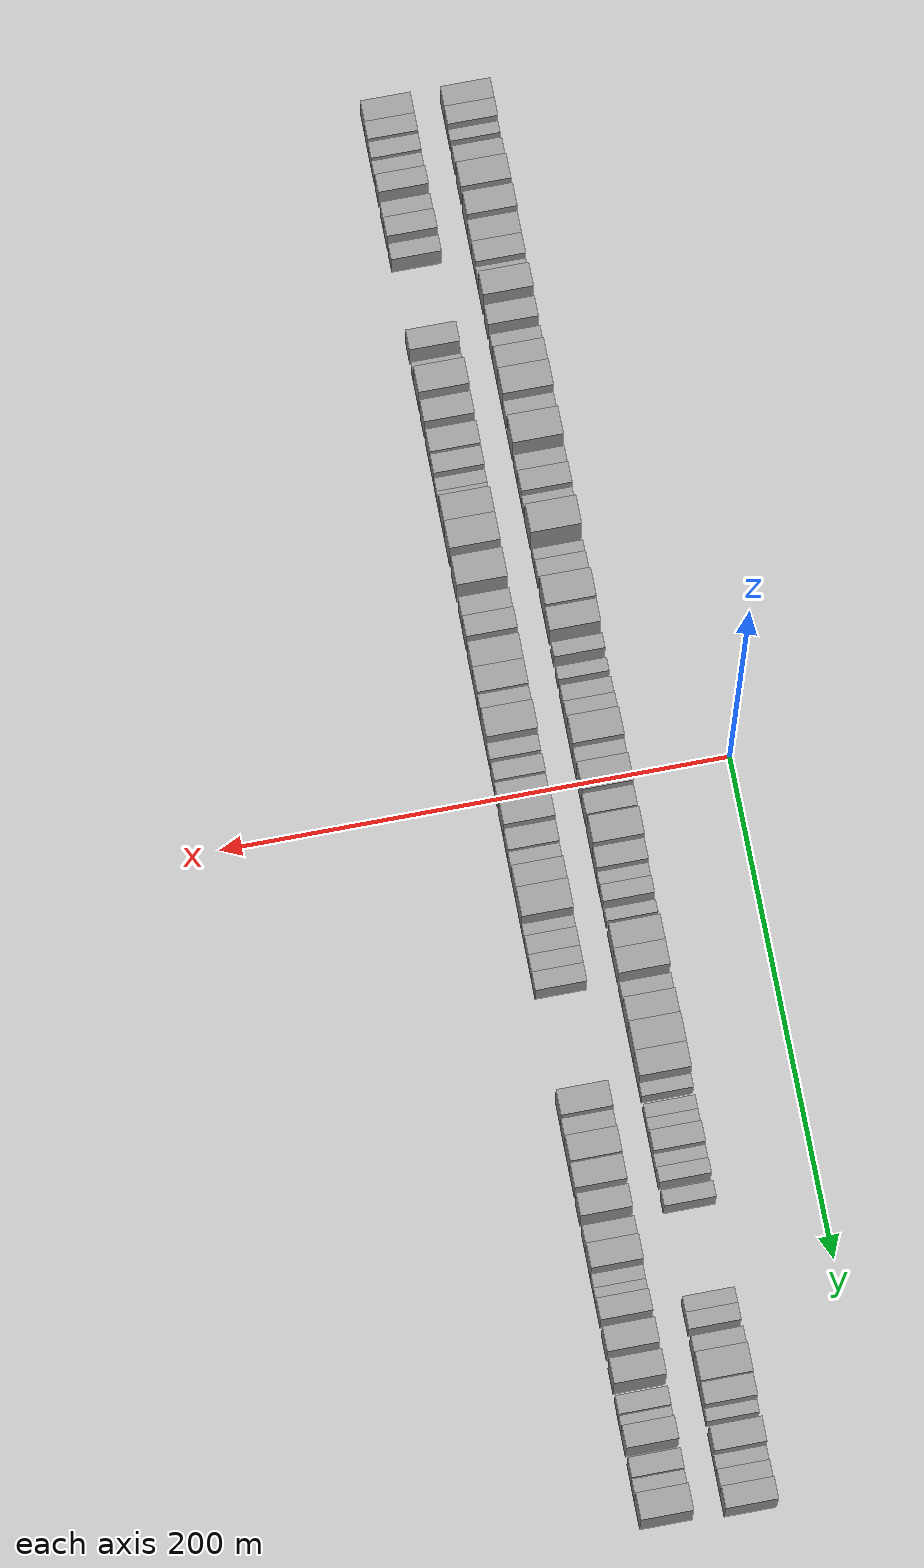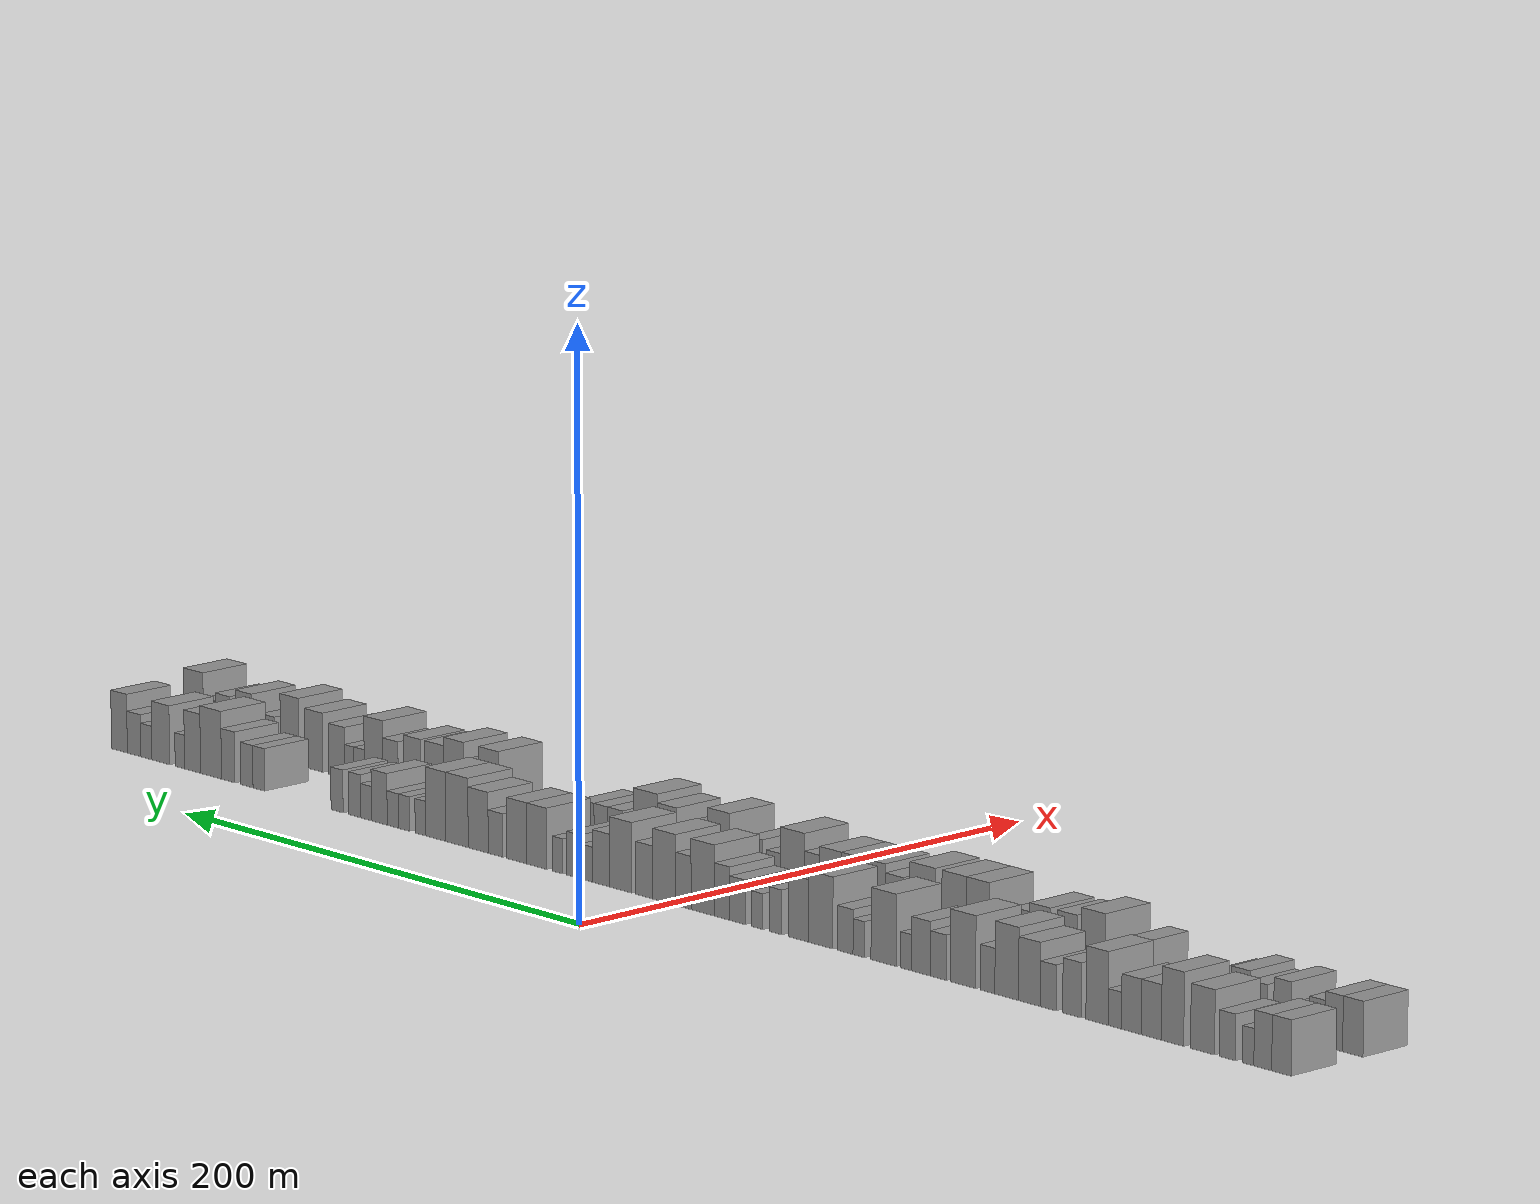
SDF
<sdf version="1.6">
 <world name="default">
  <scene>
   <sky><clouds><speed>12</speed></clouds></sky>
   <ambient>0.4 0.4 0.4 1</ambient>
   <background>0.7 0.7 0.7 1</background>
   <shadows>1</shadows>
  </scene>
  <gravity>0 0 -9.8066</gravity>
  <magnetic_field>6e-06 2.3e-05 -4.2e-05</magnetic_field>
  <physics default="0" name="default_physics" type="ode">
   <ode>
    <solver>
     <type>quick</type>
     <iters>10</iters>
     <sor>1.0</sor>
     <use_dynamic_moi_rescaling>0</use_dynamic_moi_rescaling>
    </solver>
    <constraints>
     <cfm>0</cfm>
     <erp>0.2</erp>
     <contact_max_correcting_vel>100</contact_max_correcting_vel>
     <contact_surface_layer>0.001</contact_surface_layer>
    </constraints>
   </ode>
   <max_step_size>0.004</max_step_size>
   <real_time_factor>1</real_time_factor>
   <real_time_update_rate>250</real_time_update_rate>
  </physics>
  <light name="sun" type="directional">
   <pose>0 0 10 0 0 0</pose>
   <diffuse>0.8 0.8 0.8 1</diffuse>
   <specular>0.2 0.2 0.2 1</specular>
   <attenuation>
    <range>1000</range>
    <constant>0.9</constant>
    <linear>0.01</linear>
    <quadratic>0.001</quadratic>
   </attenuation>
   <direction>-0.5 0.1 -0.9</direction>
  </light>
  <model name="building_1">
   <static>1</static>
   <pose>50.0000 -279.8190 0 0.000000 0.000000 0.000000</pose>
   <link name="link">
    <pose>0 0 9.00 0 0 0</pose>
    <collision name="collision"><geometry><box><size>20.0000 8.3619 18.0000</size></box></geometry></collision>
    <visual name="visual">
     <cast_shadows>0</cast_shadows>
     <geometry><box><size>20.0000 8.3619 18.0000</size></box></geometry>
     <material>
      <script>
       <uri>model://grey_wall/materials/scripts</uri>
       <uri>model://grey_wall/materials/textures</uri>
       <name>vrc/grey_wall</name>
      </script>
     </material>
    </visual>
   </link>
  </model>
  <model name="building_2">
   <static>1</static>
   <pose>50.0000 -271.7829 0 0.000000 0.000000 0.000000</pose>
   <link name="link">
    <pose>0 0 9.00 0 0 0</pose>
    <collision name="collision"><geometry><box><size>20.0000 7.7102 18.0000</size></box></geometry></collision>
    <visual name="visual">
     <cast_shadows>0</cast_shadows>
     <geometry><box><size>20.0000 7.7102 18.0000</size></box></geometry>
     <material>
      <script>
       <uri>model://grey_wall/materials/scripts</uri>
       <uri>model://grey_wall/materials/textures</uri>
       <name>vrc/grey_wall</name>
      </script>
     </material>
    </visual>
   </link>
  </model>
  <model name="building_3">
   <static>1</static>
   <pose>50.0000 -265.4402 0 0.000000 0.000000 0.000000</pose>
   <link name="link">
    <pose>0 0 6.00 0 0 0</pose>
    <collision name="collision"><geometry><box><size>20.0000 4.9754 12.0000</size></box></geometry></collision>
    <visual name="visual">
     <cast_shadows>0</cast_shadows>
     <geometry><box><size>20.0000 4.9754 12.0000</size></box></geometry>
     <material>
      <script>
       <uri>model://grey_wall/materials/scripts</uri>
       <uri>model://grey_wall/materials/textures</uri>
       <name>vrc/grey_wall</name>
      </script>
     </material>
    </visual>
   </link>
  </model>
  <model name="building_4">
   <static>1</static>
   <pose>50.0000 -256.4035 0 0.000000 0.000000 0.000000</pose>
   <link name="link">
    <pose>0 0 7.50 0 0 0</pose>
    <collision name="collision"><geometry><box><size>20.0000 7.0979 15.0000</size></box></geometry></collision>
    <visual name="visual">
     <cast_shadows>0</cast_shadows>
     <geometry><box><size>20.0000 7.0979 15.0000</size></box></geometry>
     <material>
      <script>
       <uri>model://grey_wall/materials/scripts</uri>
       <uri>model://grey_wall/materials/textures</uri>
       <name>vrc/grey_wall</name>
      </script>
     </material>
    </visual>
   </link>
  </model>
  <model name="building_5">
   <static>1</static>
   <pose>50.0000 -245.6082 0 0.000000 0.000000 0.000000</pose>
   <link name="link">
    <pose>0 0 10.50 0 0 0</pose>
    <collision name="collision"><geometry><box><size>20.0000 10.4927 21.0000</size></box></geometry></collision>
    <visual name="visual">
     <cast_shadows>0</cast_shadows>
     <geometry><box><size>20.0000 10.4927 21.0000</size></box></geometry>
     <material>
      <script>
       <uri>model://grey_wall/materials/scripts</uri>
       <uri>model://grey_wall/materials/textures</uri>
       <name>vrc/grey_wall</name>
      </script>
     </material>
    </visual>
   </link>
  </model>
  <model name="building_6">
   <static>1</static>
   <pose>50.0000 -232.4707 0 0.000000 0.000000 0.000000</pose>
   <link name="link">
    <pose>0 0 12.00 0 0 0</pose>
    <collision name="collision"><geometry><box><size>20.0000 9.7823 24.0000</size></box></geometry></collision>
    <visual name="visual">
     <cast_shadows>0</cast_shadows>
     <geometry><box><size>20.0000 9.7823 24.0000</size></box></geometry>
     <material>
      <script>
       <uri>model://grey_wall/materials/scripts</uri>
       <uri>model://grey_wall/materials/textures</uri>
       <name>vrc/grey_wall</name>
      </script>
     </material>
    </visual>
   </link>
  </model>
  <model name="building_7">
   <static>1</static>
   <pose>50.0000 -223.0820 0 0.000000 0.000000 0.000000</pose>
   <link name="link">
    <pose>0 0 9.00 0 0 0</pose>
    <collision name="collision"><geometry><box><size>20.0000 8.9953 18.0000</size></box></geometry></collision>
    <visual name="visual">
     <cast_shadows>0</cast_shadows>
     <geometry><box><size>20.0000 8.9953 18.0000</size></box></geometry>
     <material>
      <script>
       <uri>model://grey_wall/materials/scripts</uri>
       <uri>model://grey_wall/materials/textures</uri>
       <name>vrc/grey_wall</name>
      </script>
     </material>
    </visual>
   </link>
  </model>
  <model name="building_8">
   <static>1</static>
   <pose>50.0000 -214.2455 0 0.000000 0.000000 0.000000</pose>
   <link name="link">
    <pose>0 0 9.00 0 0 0</pose>
    <collision name="collision"><geometry><box><size>20.0000 8.6777 18.0000</size></box></geometry></collision>
    <visual name="visual">
     <cast_shadows>0</cast_shadows>
     <geometry><box><size>20.0000 8.6777 18.0000</size></box></geometry>
     <material>
      <script>
       <uri>model://grey_wall/materials/scripts</uri>
       <uri>model://grey_wall/materials/textures</uri>
       <name>vrc/grey_wall</name>
      </script>
     </material>
    </visual>
   </link>
  </model>
  <model name="building_9">
   <static>1</static>
   <pose>50.0000 -206.9102 0 0.000000 0.000000 0.000000</pose>
   <link name="link">
    <pose>0 0 6.00 0 0 0</pose>
    <collision name="collision"><geometry><box><size>20.0000 5.9929 12.0000</size></box></geometry></collision>
    <visual name="visual">
     <cast_shadows>0</cast_shadows>
     <geometry><box><size>20.0000 5.9929 12.0000</size></box></geometry>
     <material>
      <script>
       <uri>model://grey_wall/materials/scripts</uri>
       <uri>model://grey_wall/materials/textures</uri>
       <name>vrc/grey_wall</name>
      </script>
     </material>
    </visual>
   </link>
  </model>
  <model name="building_10">
   <static>1</static>
   <pose>50.0000 -198.9653 0 0.000000 0.000000 0.000000</pose>
   <link name="link">
    <pose>0 0 12.00 0 0 0</pose>
    <collision name="collision"><geometry><box><size>20.0000 9.8969 24.0000</size></box></geometry></collision>
    <visual name="visual">
     <cast_shadows>0</cast_shadows>
     <geometry><box><size>20.0000 9.8969 24.0000</size></box></geometry>
     <material>
      <script>
       <uri>model://grey_wall/materials/scripts</uri>
       <uri>model://grey_wall/materials/textures</uri>
       <name>vrc/grey_wall</name>
      </script>
     </material>
    </visual>
   </link>
  </model>
  <model name="building_11">
   <static>1</static>
   <pose>50.0000 -187.8194 0 0.000000 0.000000 0.000000</pose>
   <link name="link">
    <pose>0 0 9.00 0 0 0</pose>
    <collision name="collision"><geometry><box><size>20.0000 8.3949 18.0000</size></box></geometry></collision>
    <visual name="visual">
     <cast_shadows>0</cast_shadows>
     <geometry><box><size>20.0000 8.3949 18.0000</size></box></geometry>
     <material>
      <script>
       <uri>model://grey_wall/materials/scripts</uri>
       <uri>model://grey_wall/materials/textures</uri>
       <name>vrc/grey_wall</name>
      </script>
     </material>
    </visual>
   </link>
  </model>
  <model name="building_12">
   <static>1</static>
   <pose>50.0000 -177.0867 0 0.000000 0.000000 0.000000</pose>
   <link name="link">
    <pose>0 0 7.50 0 0 0</pose>
    <collision name="collision"><geometry><box><size>20.0000 7.0706 15.0000</size></box></geometry></collision>
    <visual name="visual">
     <cast_shadows>0</cast_shadows>
     <geometry><box><size>20.0000 7.0706 15.0000</size></box></geometry>
     <material>
      <script>
       <uri>model://grey_wall/materials/scripts</uri>
       <uri>model://grey_wall/materials/textures</uri>
       <name>vrc/grey_wall</name>
      </script>
     </material>
    </visual>
   </link>
  </model>
  <model name="building_13">
   <static>1</static>
   <pose>50.0000 -168.6290 0 0.000000 0.000000 0.000000</pose>
   <link name="link">
    <pose>0 0 10.50 0 0 0</pose>
    <collision name="collision"><geometry><box><size>20.0000 9.8448 21.0000</size></box></geometry></collision>
    <visual name="visual">
     <cast_shadows>0</cast_shadows>
     <geometry><box><size>20.0000 9.8448 21.0000</size></box></geometry>
     <material>
      <script>
       <uri>model://grey_wall/materials/scripts</uri>
       <uri>model://grey_wall/materials/textures</uri>
       <name>vrc/grey_wall</name>
      </script>
     </material>
    </visual>
   </link>
  </model>
  <model name="building_14">
   <static>1</static>
   <pose>50.0000 -158.3106 0 0.000000 0.000000 0.000000</pose>
   <link name="link">
    <pose>0 0 12.00 0 0 0</pose>
    <collision name="collision"><geometry><box><size>20.0000 10.7921 24.0000</size></box></geometry></collision>
    <visual name="visual">
     <cast_shadows>0</cast_shadows>
     <geometry><box><size>20.0000 10.7921 24.0000</size></box></geometry>
     <material>
      <script>
       <uri>model://grey_wall/materials/scripts</uri>
       <uri>model://grey_wall/materials/textures</uri>
       <name>vrc/grey_wall</name>
      </script>
     </material>
    </visual>
   </link>
  </model>
  <model name="building_15">
   <static>1</static>
   <pose>50.0000 -149.5389 0 0.000000 0.000000 0.000000</pose>
   <link name="link">
    <pose>0 0 7.50 0 0 0</pose>
    <collision name="collision"><geometry><box><size>20.0000 6.7513 15.0000</size></box></geometry></collision>
    <visual name="visual">
     <cast_shadows>0</cast_shadows>
     <geometry><box><size>20.0000 6.7513 15.0000</size></box></geometry>
     <material>
      <script>
       <uri>model://grey_wall/materials/scripts</uri>
       <uri>model://grey_wall/materials/textures</uri>
       <name>vrc/grey_wall</name>
      </script>
     </material>
    </visual>
   </link>
  </model>
  <model name="building_16">
   <static>1</static>
   <pose>50.0000 -138.3980 0 0.000000 0.000000 0.000000</pose>
   <link name="link">
    <pose>0 0 12.00 0 0 0</pose>
    <collision name="collision"><geometry><box><size>20.0000 11.5305 24.0000</size></box></geometry></collision>
    <visual name="visual">
     <cast_shadows>0</cast_shadows>
     <geometry><box><size>20.0000 11.5305 24.0000</size></box></geometry>
     <material>
      <script>
       <uri>model://grey_wall/materials/scripts</uri>
       <uri>model://grey_wall/materials/textures</uri>
       <name>vrc/grey_wall</name>
      </script>
     </material>
    </visual>
   </link>
  </model>
  <model name="building_17">
   <static>1</static>
   <pose>50.0000 -126.9144 0 0.000000 0.000000 0.000000</pose>
   <link name="link">
    <pose>0 0 7.50 0 0 0</pose>
    <collision name="collision"><geometry><box><size>20.0000 7.4367 15.0000</size></box></geometry></collision>
    <visual name="visual">
     <cast_shadows>0</cast_shadows>
     <geometry><box><size>20.0000 7.4367 15.0000</size></box></geometry>
     <material>
      <script>
       <uri>model://grey_wall/materials/scripts</uri>
       <uri>model://grey_wall/materials/textures</uri>
       <name>vrc/grey_wall</name>
      </script>
     </material>
    </visual>
   </link>
  </model>
  <model name="building_18">
   <static>1</static>
   <pose>50.0000 -118.8978 0 0.000000 0.000000 0.000000</pose>
   <link name="link">
    <pose>0 0 9.00 0 0 0</pose>
    <collision name="collision"><geometry><box><size>20.0000 8.5964 18.0000</size></box></geometry></collision>
    <visual name="visual">
     <cast_shadows>0</cast_shadows>
     <geometry><box><size>20.0000 8.5964 18.0000</size></box></geometry>
     <material>
      <script>
       <uri>model://grey_wall/materials/scripts</uri>
       <uri>model://grey_wall/materials/textures</uri>
       <name>vrc/grey_wall</name>
      </script>
     </material>
    </visual>
   </link>
  </model>
  <model name="building_19">
   <static>1</static>
   <pose>50.0000 -112.0478 0 0.000000 0.000000 0.000000</pose>
   <link name="link">
    <pose>0 0 6.00 0 0 0</pose>
    <collision name="collision"><geometry><box><size>20.0000 5.1036 12.0000</size></box></geometry></collision>
    <visual name="visual">
     <cast_shadows>0</cast_shadows>
     <geometry><box><size>20.0000 5.1036 12.0000</size></box></geometry>
     <material>
      <script>
       <uri>model://grey_wall/materials/scripts</uri>
       <uri>model://grey_wall/materials/textures</uri>
       <name>vrc/grey_wall</name>
      </script>
     </material>
    </visual>
   </link>
  </model>
  <model name="building_20">
   <static>1</static>
   <pose>50.0000 -101.6275 0 0.000000 0.000000 0.000000</pose>
   <link name="link">
    <pose>0 0 12.00 0 0 0</pose>
    <collision name="collision"><geometry><box><size>20.0000 11.7370 24.0000</size></box></geometry></collision>
    <visual name="visual">
     <cast_shadows>0</cast_shadows>
     <geometry><box><size>20.0000 11.7370 24.0000</size></box></geometry>
     <material>
      <script>
       <uri>model://grey_wall/materials/scripts</uri>
       <uri>model://grey_wall/materials/textures</uri>
       <name>vrc/grey_wall</name>
      </script>
     </material>
    </visual>
   </link>
  </model>
  <model name="building_21">
   <static>1</static>
   <pose>50.0000 -90.0536 0 0.000000 0.000000 0.000000</pose>
   <link name="link">
    <pose>0 0 6.00 0 0 0</pose>
    <collision name="collision"><geometry><box><size>20.0000 5.4109 12.0000</size></box></geometry></collision>
    <visual name="visual">
     <cast_shadows>0</cast_shadows>
     <geometry><box><size>20.0000 5.4109 12.0000</size></box></geometry>
     <material>
      <script>
       <uri>model://grey_wall/materials/scripts</uri>
       <uri>model://grey_wall/materials/textures</uri>
       <name>vrc/grey_wall</name>
      </script>
     </material>
    </visual>
   </link>
  </model>
  <model name="building_22">
   <static>1</static>
   <pose>50.0000 -83.6219 0 0.000000 0.000000 0.000000</pose>
   <link name="link">
    <pose>0 0 7.50 0 0 0</pose>
    <collision name="collision"><geometry><box><size>20.0000 7.4524 15.0000</size></box></geometry></collision>
    <visual name="visual">
     <cast_shadows>0</cast_shadows>
     <geometry><box><size>20.0000 7.4524 15.0000</size></box></geometry>
     <material>
      <script>
       <uri>model://grey_wall/materials/scripts</uri>
       <uri>model://grey_wall/materials/textures</uri>
       <name>vrc/grey_wall</name>
      </script>
     </material>
    </visual>
   </link>
  </model>
  <model name="building_23">
   <static>1</static>
   <pose>50.0000 -72.0594 0 0.000000 0.000000 0.000000</pose>
   <link name="link">
    <pose>0 0 12.00 0 0 0</pose>
    <collision name="collision"><geometry><box><size>20.0000 11.6725 24.0000</size></box></geometry></collision>
    <visual name="visual">
     <cast_shadows>0</cast_shadows>
     <geometry><box><size>20.0000 11.6725 24.0000</size></box></geometry>
     <material>
      <script>
       <uri>model://grey_wall/materials/scripts</uri>
       <uri>model://grey_wall/materials/textures</uri>
       <name>vrc/grey_wall</name>
      </script>
     </material>
    </visual>
   </link>
  </model>
  <model name="building_24">
   <static>1</static>
   <pose>50.0000 -61.4678 0 0.000000 0.000000 0.000000</pose>
   <link name="link">
    <pose>0 0 10.50 0 0 0</pose>
    <collision name="collision"><geometry><box><size>20.0000 9.5107 21.0000</size></box></geometry></collision>
    <visual name="visual">
     <cast_shadows>0</cast_shadows>
     <geometry><box><size>20.0000 9.5107 21.0000</size></box></geometry>
     <material>
      <script>
       <uri>model://grey_wall/materials/scripts</uri>
       <uri>model://grey_wall/materials/textures</uri>
       <name>vrc/grey_wall</name>
      </script>
     </material>
    </visual>
   </link>
  </model>
  <model name="building_25">
   <static>1</static>
   <pose>50.0000 -50.6916 0 0.000000 0.000000 0.000000</pose>
   <link name="link">
    <pose>0 0 7.50 0 0 0</pose>
    <collision name="collision"><geometry><box><size>20.0000 6.0417 15.0000</size></box></geometry></collision>
    <visual name="visual">
     <cast_shadows>0</cast_shadows>
     <geometry><box><size>20.0000 6.0417 15.0000</size></box></geometry>
     <material>
      <script>
       <uri>model://grey_wall/materials/scripts</uri>
       <uri>model://grey_wall/materials/textures</uri>
       <name>vrc/grey_wall</name>
      </script>
     </material>
    </visual>
   </link>
  </model>
  <model name="building_26">
   <static>1</static>
   <pose>50.0000 -41.9416 0 0.000000 0.000000 0.000000</pose>
   <link name="link">
    <pose>0 0 6.00 0 0 0</pose>
    <collision name="collision"><geometry><box><size>20.0000 5.4582 12.0000</size></box></geometry></collision>
    <visual name="visual">
     <cast_shadows>0</cast_shadows>
     <geometry><box><size>20.0000 5.4582 12.0000</size></box></geometry>
     <material>
      <script>
       <uri>model://grey_wall/materials/scripts</uri>
       <uri>model://grey_wall/materials/textures</uri>
       <name>vrc/grey_wall</name>
      </script>
     </material>
    </visual>
   </link>
  </model>
  <model name="building_27">
   <static>1</static>
   <pose>50.0000 -32.5497 0 0.000000 0.000000 0.000000</pose>
   <link name="link">
    <pose>0 0 7.50 0 0 0</pose>
    <collision name="collision"><geometry><box><size>20.0000 7.3256 15.0000</size></box></geometry></collision>
    <visual name="visual">
     <cast_shadows>0</cast_shadows>
     <geometry><box><size>20.0000 7.3256 15.0000</size></box></geometry>
     <material>
      <script>
       <uri>model://grey_wall/materials/scripts</uri>
       <uri>model://grey_wall/materials/textures</uri>
       <name>vrc/grey_wall</name>
      </script>
     </material>
    </visual>
   </link>
  </model>
  <model name="building_28">
   <static>1</static>
   <pose>50.0000 -25.1557 0 0.000000 0.000000 0.000000</pose>
   <link name="link">
    <pose>0 0 9.00 0 0 0</pose>
    <collision name="collision"><geometry><box><size>20.0000 7.4624 18.0000</size></box></geometry></collision>
    <visual name="visual">
     <cast_shadows>0</cast_shadows>
     <geometry><box><size>20.0000 7.4624 18.0000</size></box></geometry>
     <material>
      <script>
       <uri>model://grey_wall/materials/scripts</uri>
       <uri>model://grey_wall/materials/textures</uri>
       <name>vrc/grey_wall</name>
      </script>
     </material>
    </visual>
   </link>
  </model>
  <model name="building_29">
   <static>1</static>
   <pose>50.0000 -15.7782 0 0.000000 0.000000 0.000000</pose>
   <link name="link">
    <pose>0 0 12.00 0 0 0</pose>
    <collision name="collision"><geometry><box><size>20.0000 11.2925 24.0000</size></box></geometry></collision>
    <visual name="visual">
     <cast_shadows>0</cast_shadows>
     <geometry><box><size>20.0000 11.2925 24.0000</size></box></geometry>
     <material>
      <script>
       <uri>model://grey_wall/materials/scripts</uri>
       <uri>model://grey_wall/materials/textures</uri>
       <name>vrc/grey_wall</name>
      </script>
     </material>
    </visual>
   </link>
  </model>
  <model name="building_30">
   <static>1</static>
   <pose>50.0000 -6.4503 0 0.000000 0.000000 0.000000</pose>
   <link name="link">
    <pose>0 0 9.00 0 0 0</pose>
    <collision name="collision"><geometry><box><size>20.0000 7.3634 18.0000</size></box></geometry></collision>
    <visual name="visual">
     <cast_shadows>0</cast_shadows>
     <geometry><box><size>20.0000 7.3634 18.0000</size></box></geometry>
     <material>
      <script>
       <uri>model://grey_wall/materials/scripts</uri>
       <uri>model://grey_wall/materials/textures</uri>
       <name>vrc/grey_wall</name>
      </script>
     </material>
    </visual>
   </link>
  </model>
  <model name="building_31">
   <static>1</static>
   <pose>50.0000 2.8149 0 0.000000 0.000000 0.000000</pose>
   <link name="link">
    <pose>0 0 12.00 0 0 0</pose>
    <collision name="collision"><geometry><box><size>20.0000 11.1670 24.0000</size></box></geometry></collision>
    <visual name="visual">
     <cast_shadows>0</cast_shadows>
     <geometry><box><size>20.0000 11.1670 24.0000</size></box></geometry>
     <material>
      <script>
       <uri>model://grey_wall/materials/scripts</uri>
       <uri>model://grey_wall/materials/textures</uri>
       <name>vrc/grey_wall</name>
      </script>
     </material>
    </visual>
   </link>
  </model>
  <model name="building_32">
   <static>1</static>
   <pose>50.0000 12.5977 0 0.000000 0.000000 0.000000</pose>
   <link name="link">
    <pose>0 0 9.00 0 0 0</pose>
    <collision name="collision"><geometry><box><size>20.0000 8.3987 18.0000</size></box></geometry></collision>
    <visual name="visual">
     <cast_shadows>0</cast_shadows>
     <geometry><box><size>20.0000 8.3987 18.0000</size></box></geometry>
     <material>
      <script>
       <uri>model://grey_wall/materials/scripts</uri>
       <uri>model://grey_wall/materials/textures</uri>
       <name>vrc/grey_wall</name>
      </script>
     </material>
    </visual>
   </link>
  </model>
  <model name="building_33">
   <static>1</static>
   <pose>50.0000 24.3071 0 0.000000 0.000000 0.000000</pose>
   <link name="link">
    <pose>0 0 12.00 0 0 0</pose>
    <collision name="collision"><geometry><box><size>20.0000 11.0200 24.0000</size></box></geometry></collision>
    <visual name="visual">
     <cast_shadows>0</cast_shadows>
     <geometry><box><size>20.0000 11.0200 24.0000</size></box></geometry>
     <material>
      <script>
       <uri>model://grey_wall/materials/scripts</uri>
       <uri>model://grey_wall/materials/textures</uri>
       <name>vrc/grey_wall</name>
      </script>
     </material>
    </visual>
   </link>
  </model>
  <model name="building_34">
   <static>1</static>
   <pose>50.0000 34.0459 0 0.000000 0.000000 0.000000</pose>
   <link name="link">
    <pose>0 0 9.00 0 0 0</pose>
    <collision name="collision"><geometry><box><size>20.0000 8.4576 18.0000</size></box></geometry></collision>
    <visual name="visual">
     <cast_shadows>0</cast_shadows>
     <geometry><box><size>20.0000 8.4576 18.0000</size></box></geometry>
     <material>
      <script>
       <uri>model://grey_wall/materials/scripts</uri>
       <uri>model://grey_wall/materials/textures</uri>
       <name>vrc/grey_wall</name>
      </script>
     </material>
    </visual>
   </link>
  </model>
  <model name="building_35">
   <static>1</static>
   <pose>50.0000 41.2181 0 0.000000 0.000000 0.000000</pose>
   <link name="link">
    <pose>0 0 6.00 0 0 0</pose>
    <collision name="collision"><geometry><box><size>20.0000 5.8868 12.0000</size></box></geometry></collision>
    <visual name="visual">
     <cast_shadows>0</cast_shadows>
     <geometry><box><size>20.0000 5.8868 12.0000</size></box></geometry>
     <material>
      <script>
       <uri>model://grey_wall/materials/scripts</uri>
       <uri>model://grey_wall/materials/textures</uri>
       <name>vrc/grey_wall</name>
      </script>
     </material>
    </visual>
   </link>
  </model>
  <model name="building_36">
   <static>1</static>
   <pose>50.0000 47.5665 0 0.000000 0.000000 0.000000</pose>
   <link name="link">
    <pose>0 0 7.50 0 0 0</pose>
    <collision name="collision"><geometry><box><size>20.0000 6.8100 15.0000</size></box></geometry></collision>
    <visual name="visual">
     <cast_shadows>0</cast_shadows>
     <geometry><box><size>20.0000 6.8100 15.0000</size></box></geometry>
     <material>
      <script>
       <uri>model://grey_wall/materials/scripts</uri>
       <uri>model://grey_wall/materials/textures</uri>
       <name>vrc/grey_wall</name>
      </script>
     </material>
    </visual>
   </link>
  </model>
  <model name="building_37">
   <static>1</static>
   <pose>50.0000 55.5154 0 0.000000 0.000000 0.000000</pose>
   <link name="link">
    <pose>0 0 6.00 0 0 0</pose>
    <collision name="collision"><geometry><box><size>20.0000 5.0878 12.0000</size></box></geometry></collision>
    <visual name="visual">
     <cast_shadows>0</cast_shadows>
     <geometry><box><size>20.0000 5.0878 12.0000</size></box></geometry>
     <material>
      <script>
       <uri>model://grey_wall/materials/scripts</uri>
       <uri>model://grey_wall/materials/textures</uri>
       <name>vrc/grey_wall</name>
      </script>
     </material>
    </visual>
   </link>
  </model>
  <model name="building_38">
   <static>1</static>
   <pose>50.0000 66.0061 0 0.000000 0.000000 0.000000</pose>
   <link name="link">
    <pose>0 0 10.50 0 0 0</pose>
    <collision name="collision"><geometry><box><size>20.0000 9.8937 21.0000</size></box></geometry></collision>
    <visual name="visual">
     <cast_shadows>0</cast_shadows>
     <geometry><box><size>20.0000 9.8937 21.0000</size></box></geometry>
     <material>
      <script>
       <uri>model://grey_wall/materials/scripts</uri>
       <uri>model://grey_wall/materials/textures</uri>
       <name>vrc/grey_wall</name>
      </script>
     </material>
    </visual>
   </link>
  </model>
  <model name="building_39">
   <static>1</static>
   <pose>50.0000 75.9395 0 0.000000 0.000000 0.000000</pose>
   <link name="link">
    <pose>0 0 10.50 0 0 0</pose>
    <collision name="collision"><geometry><box><size>20.0000 9.9730 21.0000</size></box></geometry></collision>
    <visual name="visual">
     <cast_shadows>0</cast_shadows>
     <geometry><box><size>20.0000 9.9730 21.0000</size></box></geometry>
     <material>
      <script>
       <uri>model://grey_wall/materials/scripts</uri>
       <uri>model://grey_wall/materials/textures</uri>
       <name>vrc/grey_wall</name>
      </script>
     </material>
    </visual>
   </link>
  </model>
  <model name="building_40">
   <static>1</static>
   <pose>50.0000 86.6181 0 0.000000 0.000000 0.000000</pose>
   <link name="link">
    <pose>0 0 7.50 0 0 0</pose>
    <collision name="collision"><geometry><box><size>20.0000 7.3843 15.0000</size></box></geometry></collision>
    <visual name="visual">
     <cast_shadows>0</cast_shadows>
     <geometry><box><size>20.0000 7.3843 15.0000</size></box></geometry>
     <material>
      <script>
       <uri>model://grey_wall/materials/scripts</uri>
       <uri>model://grey_wall/materials/textures</uri>
       <name>vrc/grey_wall</name>
      </script>
     </material>
    </visual>
   </link>
  </model>
  <model name="building_41">
   <static>1</static>
   <pose>50.0000 95.3826 0 0.000000 0.000000 0.000000</pose>
   <link name="link">
    <pose>0 0 10.50 0 0 0</pose>
    <collision name="collision"><geometry><box><size>20.0000 10.1447 21.0000</size></box></geometry></collision>
    <visual name="visual">
     <cast_shadows>0</cast_shadows>
     <geometry><box><size>20.0000 10.1447 21.0000</size></box></geometry>
     <material>
      <script>
       <uri>model://grey_wall/materials/scripts</uri>
       <uri>model://grey_wall/materials/textures</uri>
       <name>vrc/grey_wall</name>
      </script>
     </material>
    </visual>
   </link>
  </model>
  <model name="building_42">
   <static>1</static>
   <pose>50.0000 106.2034 0 0.000000 0.000000 0.000000</pose>
   <link name="link">
    <pose>0 0 12.00 0 0 0</pose>
    <collision name="collision"><geometry><box><size>20.0000 11.4968 24.0000</size></box></geometry></collision>
    <visual name="visual">
     <cast_shadows>0</cast_shadows>
     <geometry><box><size>20.0000 11.4968 24.0000</size></box></geometry>
     <material>
      <script>
       <uri>model://grey_wall/materials/scripts</uri>
       <uri>model://grey_wall/materials/textures</uri>
       <name>vrc/grey_wall</name>
      </script>
     </material>
    </visual>
   </link>
  </model>
  <model name="building_43">
   <static>1</static>
   <pose>50.0000 117.0278 0 0.000000 0.000000 0.000000</pose>
   <link name="link">
    <pose>0 0 12.00 0 0 0</pose>
    <collision name="collision"><geometry><box><size>20.0000 10.1520 24.0000</size></box></geometry></collision>
    <visual name="visual">
     <cast_shadows>0</cast_shadows>
     <geometry><box><size>20.0000 10.1520 24.0000</size></box></geometry>
     <material>
      <script>
       <uri>model://grey_wall/materials/scripts</uri>
       <uri>model://grey_wall/materials/textures</uri>
       <name>vrc/grey_wall</name>
      </script>
     </material>
    </visual>
   </link>
  </model>
  <model name="building_44">
   <static>1</static>
   <pose>50.0000 124.8269 0 0.000000 0.000000 0.000000</pose>
   <link name="link">
    <pose>0 0 6.00 0 0 0</pose>
    <collision name="collision"><geometry><box><size>20.0000 5.4463 12.0000</size></box></geometry></collision>
    <visual name="visual">
     <cast_shadows>0</cast_shadows>
     <geometry><box><size>20.0000 5.4463 12.0000</size></box></geometry>
     <material>
      <script>
       <uri>model://grey_wall/materials/scripts</uri>
       <uri>model://grey_wall/materials/textures</uri>
       <name>vrc/grey_wall</name>
      </script>
     </material>
    </visual>
   </link>
  </model>
  <model name="building_45">
   <static>1</static>
   <pose>50.0000 133.2887 0 0.000000 0.000000 0.000000</pose>
   <link name="link">
    <pose>0 0 6.00 0 0 0</pose>
    <collision name="collision"><geometry><box><size>20.0000 5.4773 12.0000</size></box></geometry></collision>
    <visual name="visual">
     <cast_shadows>0</cast_shadows>
     <geometry><box><size>20.0000 5.4773 12.0000</size></box></geometry>
     <material>
      <script>
       <uri>model://grey_wall/materials/scripts</uri>
       <uri>model://grey_wall/materials/textures</uri>
       <name>vrc/grey_wall</name>
      </script>
     </material>
    </visual>
   </link>
  </model>
  <model name="building_46">
   <static>1</static>
   <pose>50.0000 138.9892 0 0.000000 0.000000 0.000000</pose>
   <link name="link">
    <pose>0 0 6.00 0 0 0</pose>
    <collision name="collision"><geometry><box><size>20.0000 5.9235 12.0000</size></box></geometry></collision>
    <visual name="visual">
     <cast_shadows>0</cast_shadows>
     <geometry><box><size>20.0000 5.9235 12.0000</size></box></geometry>
     <material>
      <script>
       <uri>model://grey_wall/materials/scripts</uri>
       <uri>model://grey_wall/materials/textures</uri>
       <name>vrc/grey_wall</name>
      </script>
     </material>
    </visual>
   </link>
  </model>
  <model name="building_47">
   <static>1</static>
   <pose>50.0000 146.0393 0 0.000000 0.000000 0.000000</pose>
   <link name="link">
    <pose>0 0 9.00 0 0 0</pose>
    <collision name="collision"><geometry><box><size>20.0000 8.1767 18.0000</size></box></geometry></collision>
    <visual name="visual">
     <cast_shadows>0</cast_shadows>
     <geometry><box><size>20.0000 8.1767 18.0000</size></box></geometry>
     <material>
      <script>
       <uri>model://grey_wall/materials/scripts</uri>
       <uri>model://grey_wall/materials/textures</uri>
       <name>vrc/grey_wall</name>
      </script>
     </material>
    </visual>
   </link>
  </model>
  <model name="building_48">
   <static>1</static>
   <pose>50.0000 152.9805 0 0.000000 0.000000 0.000000</pose>
   <link name="link">
    <pose>0 0 6.00 0 0 0</pose>
    <collision name="collision"><geometry><box><size>20.0000 5.7057 12.0000</size></box></geometry></collision>
    <visual name="visual">
     <cast_shadows>0</cast_shadows>
     <geometry><box><size>20.0000 5.7057 12.0000</size></box></geometry>
     <material>
      <script>
       <uri>model://grey_wall/materials/scripts</uri>
       <uri>model://grey_wall/materials/textures</uri>
       <name>vrc/grey_wall</name>
      </script>
     </material>
    </visual>
   </link>
  </model>
  <model name="building_49">
   <static>1</static>
   <pose>50.0000 158.8335 0 0.000000 0.000000 0.000000</pose>
   <link name="link">
    <pose>0 0 7.50 0 0 0</pose>
    <collision name="collision"><geometry><box><size>20.0000 6.0004 15.0000</size></box></geometry></collision>
    <visual name="visual">
     <cast_shadows>0</cast_shadows>
     <geometry><box><size>20.0000 6.0004 15.0000</size></box></geometry>
     <material>
      <script>
       <uri>model://grey_wall/materials/scripts</uri>
       <uri>model://grey_wall/materials/textures</uri>
       <name>vrc/grey_wall</name>
      </script>
     </material>
    </visual>
   </link>
  </model>
  <model name="building_50">
   <static>1</static>
   <pose>50.0000 167.9812 0 0.000000 0.000000 0.000000</pose>
   <link name="link">
    <pose>0 0 7.50 0 0 0</pose>
    <collision name="collision"><geometry><box><size>20.0000 6.2950 15.0000</size></box></geometry></collision>
    <visual name="visual">
     <cast_shadows>0</cast_shadows>
     <geometry><box><size>20.0000 6.2950 15.0000</size></box></geometry>
     <material>
      <script>
       <uri>model://grey_wall/materials/scripts</uri>
       <uri>model://grey_wall/materials/textures</uri>
       <name>vrc/grey_wall</name>
      </script>
     </material>
    </visual>
   </link>
  </model>
  <model name="building_51">
   <static>1</static>
   <pose>50.0000 209.2563 0 0.000000 0.000000 0.000000</pose>
   <link name="link">
    <pose>0 0 7.50 0 0 0</pose>
    <collision name="collision"><geometry><box><size>20.0000 6.0850 15.0000</size></box></geometry></collision>
    <visual name="visual">
     <cast_shadows>0</cast_shadows>
     <geometry><box><size>20.0000 6.0850 15.0000</size></box></geometry>
     <material>
      <script>
       <uri>model://grey_wall/materials/scripts</uri>
       <uri>model://grey_wall/materials/textures</uri>
       <name>vrc/grey_wall</name>
      </script>
     </material>
    </visual>
   </link>
  </model>
  <model name="building_52">
   <static>1</static>
   <pose>50.0000 215.6219 0 0.000000 0.000000 0.000000</pose>
   <link name="link">
    <pose>0 0 7.50 0 0 0</pose>
    <collision name="collision"><geometry><box><size>20.0000 6.6463 15.0000</size></box></geometry></collision>
    <visual name="visual">
     <cast_shadows>0</cast_shadows>
     <geometry><box><size>20.0000 6.6463 15.0000</size></box></geometry>
     <material>
      <script>
       <uri>model://grey_wall/materials/scripts</uri>
       <uri>model://grey_wall/materials/textures</uri>
       <name>vrc/grey_wall</name>
      </script>
     </material>
    </visual>
   </link>
  </model>
  <model name="building_53">
   <static>1</static>
   <pose>50.0000 225.5456 0 0.000000 0.000000 0.000000</pose>
   <link name="link">
    <pose>0 0 9.00 0 0 0</pose>
    <collision name="collision"><geometry><box><size>20.0000 7.2011 18.0000</size></box></geometry></collision>
    <visual name="visual">
     <cast_shadows>0</cast_shadows>
     <geometry><box><size>20.0000 7.2011 18.0000</size></box></geometry>
     <material>
      <script>
       <uri>model://grey_wall/materials/scripts</uri>
       <uri>model://grey_wall/materials/textures</uri>
       <name>vrc/grey_wall</name>
      </script>
     </material>
    </visual>
   </link>
  </model>
  <model name="building_54">
   <static>1</static>
   <pose>50.0000 234.7607 0 0.000000 0.000000 0.000000</pose>
   <link name="link">
    <pose>0 0 12.00 0 0 0</pose>
    <collision name="collision"><geometry><box><size>20.0000 11.2290 24.0000</size></box></geometry></collision>
    <visual name="visual">
     <cast_shadows>0</cast_shadows>
     <geometry><box><size>20.0000 11.2290 24.0000</size></box></geometry>
     <material>
      <script>
       <uri>model://grey_wall/materials/scripts</uri>
       <uri>model://grey_wall/materials/textures</uri>
       <name>vrc/grey_wall</name>
      </script>
     </material>
    </visual>
   </link>
  </model>
  <model name="building_55">
   <static>1</static>
   <pose>50.0000 244.6903 0 0.000000 0.000000 0.000000</pose>
   <link name="link">
    <pose>0 0 10.50 0 0 0</pose>
    <collision name="collision"><geometry><box><size>20.0000 8.6302 21.0000</size></box></geometry></collision>
    <visual name="visual">
     <cast_shadows>0</cast_shadows>
     <geometry><box><size>20.0000 8.6302 21.0000</size></box></geometry>
     <material>
      <script>
       <uri>model://grey_wall/materials/scripts</uri>
       <uri>model://grey_wall/materials/textures</uri>
       <name>vrc/grey_wall</name>
      </script>
     </material>
    </visual>
   </link>
  </model>
  <model name="building_56">
   <static>1</static>
   <pose>50.0000 251.5346 0 0.000000 0.000000 0.000000</pose>
   <link name="link">
    <pose>0 0 6.00 0 0 0</pose>
    <collision name="collision"><geometry><box><size>20.0000 5.0584 12.0000</size></box></geometry></collision>
    <visual name="visual">
     <cast_shadows>0</cast_shadows>
     <geometry><box><size>20.0000 5.0584 12.0000</size></box></geometry>
     <material>
      <script>
       <uri>model://grey_wall/materials/scripts</uri>
       <uri>model://grey_wall/materials/textures</uri>
       <name>vrc/grey_wall</name>
      </script>
     </material>
    </visual>
   </link>
  </model>
  <model name="building_57">
   <static>1</static>
   <pose>50.0000 261.9085 0 0.000000 0.000000 0.000000</pose>
   <link name="link">
    <pose>0 0 10.50 0 0 0</pose>
    <collision name="collision"><geometry><box><size>20.0000 9.6893 21.0000</size></box></geometry></collision>
    <visual name="visual">
     <cast_shadows>0</cast_shadows>
     <geometry><box><size>20.0000 9.6893 21.0000</size></box></geometry>
     <material>
      <script>
       <uri>model://grey_wall/materials/scripts</uri>
       <uri>model://grey_wall/materials/textures</uri>
       <name>vrc/grey_wall</name>
      </script>
     </material>
    </visual>
   </link>
  </model>
  <model name="building_58">
   <static>1</static>
   <pose>50.0000 269.7282 0 0.000000 0.000000 0.000000</pose>
   <link name="link">
    <pose>0 0 6.00 0 0 0</pose>
    <collision name="collision"><geometry><box><size>20.0000 5.9503 12.0000</size></box></geometry></collision>
    <visual name="visual">
     <cast_shadows>0</cast_shadows>
     <geometry><box><size>20.0000 5.9503 12.0000</size></box></geometry>
     <material>
      <script>
       <uri>model://grey_wall/materials/scripts</uri>
       <uri>model://grey_wall/materials/textures</uri>
       <name>vrc/grey_wall</name>
      </script>
     </material>
    </visual>
   </link>
  </model>
  <model name="building_59">
   <static>1</static>
   <pose>50.0000 276.3991 0 0.000000 0.000000 0.000000</pose>
   <link name="link">
    <pose>0 0 7.50 0 0 0</pose>
    <collision name="collision"><geometry><box><size>20.0000 7.3915 15.0000</size></box></geometry></collision>
    <visual name="visual">
     <cast_shadows>0</cast_shadows>
     <geometry><box><size>20.0000 7.3915 15.0000</size></box></geometry>
     <material>
      <script>
       <uri>model://grey_wall/materials/scripts</uri>
       <uri>model://grey_wall/materials/textures</uri>
       <name>vrc/grey_wall</name>
      </script>
     </material>
    </visual>
   </link>
  </model>
  <model name="building_60">
   <static>1</static>
   <pose>50.0000 284.4112 0 0.000000 0.000000 0.000000</pose>
   <link name="link">
    <pose>0 0 10.50 0 0 0</pose>
    <collision name="collision"><geometry><box><size>20.0000 8.6327 21.0000</size></box></geometry></collision>
    <visual name="visual">
     <cast_shadows>0</cast_shadows>
     <geometry><box><size>20.0000 8.6327 21.0000</size></box></geometry>
     <material>
      <script>
       <uri>model://grey_wall/materials/scripts</uri>
       <uri>model://grey_wall/materials/textures</uri>
       <name>vrc/grey_wall</name>
      </script>
     </material>
    </visual>
   </link>
  </model>
  <model name="building_61">
   <static>1</static>
   <pose>82.0000 -279.6116 0 0.000000 0.000000 0.000000</pose>
   <link name="link">
    <pose>0 0 9.00 0 0 0</pose>
    <collision name="collision"><geometry><box><size>20.0000 8.7768 18.0000</size></box></geometry></collision>
    <visual name="visual">
     <cast_shadows>0</cast_shadows>
     <geometry><box><size>20.0000 8.7768 18.0000</size></box></geometry>
     <material>
      <script>
       <uri>model://grey_wall/materials/scripts</uri>
       <uri>model://grey_wall/materials/textures</uri>
       <name>vrc/grey_wall</name>
      </script>
     </material>
    </visual>
   </link>
  </model>
  <model name="building_62">
   <static>1</static>
   <pose>82.0000 -271.4348 0 0.000000 0.000000 0.000000</pose>
   <link name="link">
    <pose>0 0 9.00 0 0 0</pose>
    <collision name="collision"><geometry><box><size>20.0000 7.5769 18.0000</size></box></geometry></collision>
    <visual name="visual">
     <cast_shadows>0</cast_shadows>
     <geometry><box><size>20.0000 7.5769 18.0000</size></box></geometry>
     <material>
      <script>
       <uri>model://grey_wall/materials/scripts</uri>
       <uri>model://grey_wall/materials/textures</uri>
       <name>vrc/grey_wall</name>
      </script>
     </material>
    </visual>
   </link>
  </model>
  <model name="building_63">
   <static>1</static>
   <pose>82.0000 -264.1748 0 0.000000 0.000000 0.000000</pose>
   <link name="link">
    <pose>0 0 7.50 0 0 0</pose>
    <collision name="collision"><geometry><box><size>20.0000 6.9432 15.0000</size></box></geometry></collision>
    <visual name="visual">
     <cast_shadows>0</cast_shadows>
     <geometry><box><size>20.0000 6.9432 15.0000</size></box></geometry>
     <material>
      <script>
       <uri>model://grey_wall/materials/scripts</uri>
       <uri>model://grey_wall/materials/textures</uri>
       <name>vrc/grey_wall</name>
      </script>
     </material>
    </visual>
   </link>
  </model>
  <model name="building_64">
   <static>1</static>
   <pose>82.0000 -257.7788 0 0.000000 0.000000 0.000000</pose>
   <link name="link">
    <pose>0 0 6.00 0 0 0</pose>
    <collision name="collision"><geometry><box><size>20.0000 5.8489 12.0000</size></box></geometry></collision>
    <visual name="visual">
     <cast_shadows>0</cast_shadows>
     <geometry><box><size>20.0000 5.8489 12.0000</size></box></geometry>
     <material>
      <script>
       <uri>model://grey_wall/materials/scripts</uri>
       <uri>model://grey_wall/materials/textures</uri>
       <name>vrc/grey_wall</name>
      </script>
     </material>
    </visual>
   </link>
  </model>
  <model name="building_65">
   <static>1</static>
   <pose>82.0000 -249.0392 0 0.000000 0.000000 0.000000</pose>
   <link name="link">
    <pose>0 0 9.00 0 0 0</pose>
    <collision name="collision"><geometry><box><size>20.0000 7.6304 18.0000</size></box></geometry></collision>
    <visual name="visual">
     <cast_shadows>0</cast_shadows>
     <geometry><box><size>20.0000 7.6304 18.0000</size></box></geometry>
     <material>
      <script>
       <uri>model://grey_wall/materials/scripts</uri>
       <uri>model://grey_wall/materials/textures</uri>
       <name>vrc/grey_wall</name>
      </script>
     </material>
    </visual>
   </link>
  </model>
  <model name="building_66">
   <static>1</static>
   <pose>82.0000 -238.4993 0 0.000000 0.000000 0.000000</pose>
   <link name="link">
    <pose>0 0 7.50 0 0 0</pose>
    <collision name="collision"><geometry><box><size>20.0000 7.4493 15.0000</size></box></geometry></collision>
    <visual name="visual">
     <cast_shadows>0</cast_shadows>
     <geometry><box><size>20.0000 7.4493 15.0000</size></box></geometry>
     <material>
      <script>
       <uri>model://grey_wall/materials/scripts</uri>
       <uri>model://grey_wall/materials/textures</uri>
       <name>vrc/grey_wall</name>
      </script>
     </material>
    </visual>
   </link>
  </model>
  <model name="building_67">
   <static>1</static>
   <pose>82.0000 -230.7380 0 0.000000 0.000000 0.000000</pose>
   <link name="link">
    <pose>0 0 9.00 0 0 0</pose>
    <collision name="collision"><geometry><box><size>20.0000 8.0734 18.0000</size></box></geometry></collision>
    <visual name="visual">
     <cast_shadows>0</cast_shadows>
     <geometry><box><size>20.0000 8.0734 18.0000</size></box></geometry>
     <material>
      <script>
       <uri>model://grey_wall/materials/scripts</uri>
       <uri>model://grey_wall/materials/textures</uri>
       <name>vrc/grey_wall</name>
      </script>
     </material>
    </visual>
   </link>
  </model>
  <model name="building_68">
   <static>1</static>
   <pose>82.0000 -221.3300 0 0.000000 0.000000 0.000000</pose>
   <link name="link">
    <pose>0 0 7.50 0 0 0</pose>
    <collision name="collision"><geometry><box><size>20.0000 6.7426 15.0000</size></box></geometry></collision>
    <visual name="visual">
     <cast_shadows>0</cast_shadows>
     <geometry><box><size>20.0000 6.7426 15.0000</size></box></geometry>
     <material>
      <script>
       <uri>model://grey_wall/materials/scripts</uri>
       <uri>model://grey_wall/materials/textures</uri>
       <name>vrc/grey_wall</name>
      </script>
     </material>
    </visual>
   </link>
  </model>
  <model name="building_69">
   <static>1</static>
   <pose>82.0000 -183.3673 0 0.000000 0.000000 0.000000</pose>
   <link name="link">
    <pose>0 0 9.00 0 0 0</pose>
    <collision name="collision"><geometry><box><size>20.0000 8.3942 18.0000</size></box></geometry></collision>
    <visual name="visual">
     <cast_shadows>0</cast_shadows>
     <geometry><box><size>20.0000 8.3942 18.0000</size></box></geometry>
     <material>
      <script>
       <uri>model://grey_wall/materials/scripts</uri>
       <uri>model://grey_wall/materials/textures</uri>
       <name>vrc/grey_wall</name>
      </script>
     </material>
    </visual>
   </link>
  </model>
  <model name="building_70">
   <static>1</static>
   <pose>82.0000 -173.2988 0 0.000000 0.000000 0.000000</pose>
   <link name="link">
    <pose>0 0 6.00 0 0 0</pose>
    <collision name="collision"><geometry><box><size>20.0000 5.7428 12.0000</size></box></geometry></collision>
    <visual name="visual">
     <cast_shadows>0</cast_shadows>
     <geometry><box><size>20.0000 5.7428 12.0000</size></box></geometry>
     <material>
      <script>
       <uri>model://grey_wall/materials/scripts</uri>
       <uri>model://grey_wall/materials/textures</uri>
       <name>vrc/grey_wall</name>
      </script>
     </material>
    </visual>
   </link>
  </model>
  <model name="building_71">
   <static>1</static>
   <pose>82.0000 -164.9844 0 0.000000 0.000000 0.000000</pose>
   <link name="link">
    <pose>0 0 12.00 0 0 0</pose>
    <collision name="collision"><geometry><box><size>20.0000 10.8860 24.0000</size></box></geometry></collision>
    <visual name="visual">
     <cast_shadows>0</cast_shadows>
     <geometry><box><size>20.0000 10.8860 24.0000</size></box></geometry>
     <material>
      <script>
       <uri>model://grey_wall/materials/scripts</uri>
       <uri>model://grey_wall/materials/textures</uri>
       <name>vrc/grey_wall</name>
      </script>
     </material>
    </visual>
   </link>
  </model>
  <model name="building_72">
   <static>1</static>
   <pose>82.0000 -152.9470 0 0.000000 0.000000 0.000000</pose>
   <link name="link">
    <pose>0 0 10.50 0 0 0</pose>
    <collision name="collision"><geometry><box><size>20.0000 9.1887 21.0000</size></box></geometry></collision>
    <visual name="visual">
     <cast_shadows>0</cast_shadows>
     <geometry><box><size>20.0000 9.1887 21.0000</size></box></geometry>
     <material>
      <script>
       <uri>model://grey_wall/materials/scripts</uri>
       <uri>model://grey_wall/materials/textures</uri>
       <name>vrc/grey_wall</name>
      </script>
     </material>
    </visual>
   </link>
  </model>
  <model name="building_73">
   <static>1</static>
   <pose>82.0000 -140.6547 0 0.000000 0.000000 0.000000</pose>
   <link name="link">
    <pose>0 0 10.50 0 0 0</pose>
    <collision name="collision"><geometry><box><size>20.0000 9.3959 21.0000</size></box></geometry></collision>
    <visual name="visual">
     <cast_shadows>0</cast_shadows>
     <geometry><box><size>20.0000 9.3959 21.0000</size></box></geometry>
     <material>
      <script>
       <uri>model://grey_wall/materials/scripts</uri>
       <uri>model://grey_wall/materials/textures</uri>
       <name>vrc/grey_wall</name>
      </script>
     </material>
    </visual>
   </link>
  </model>
  <model name="building_74">
   <static>1</static>
   <pose>82.0000 -132.0111 0 0.000000 0.000000 0.000000</pose>
   <link name="link">
    <pose>0 0 9.00 0 0 0</pose>
    <collision name="collision"><geometry><box><size>20.0000 7.8913 18.0000</size></box></geometry></collision>
    <visual name="visual">
     <cast_shadows>0</cast_shadows>
     <geometry><box><size>20.0000 7.8913 18.0000</size></box></geometry>
     <material>
      <script>
       <uri>model://grey_wall/materials/scripts</uri>
       <uri>model://grey_wall/materials/textures</uri>
       <name>vrc/grey_wall</name>
      </script>
     </material>
    </visual>
   </link>
  </model>
  <model name="building_75">
   <static>1</static>
   <pose>82.0000 -125.3163 0 0.000000 0.000000 0.000000</pose>
   <link name="link">
    <pose>0 0 6.00 0 0 0</pose>
    <collision name="collision"><geometry><box><size>20.0000 5.4982 12.0000</size></box></geometry></collision>
    <visual name="visual">
     <cast_shadows>0</cast_shadows>
     <geometry><box><size>20.0000 5.4982 12.0000</size></box></geometry>
     <material>
      <script>
       <uri>model://grey_wall/materials/scripts</uri>
       <uri>model://grey_wall/materials/textures</uri>
       <name>vrc/grey_wall</name>
      </script>
     </material>
    </visual>
   </link>
  </model>
  <model name="building_76">
   <static>1</static>
   <pose>82.0000 -119.8994 0 0.000000 0.000000 0.000000</pose>
   <link name="link">
    <pose>0 0 6.00 0 0 0</pose>
    <collision name="collision"><geometry><box><size>20.0000 5.3358 12.0000</size></box></geometry></collision>
    <visual name="visual">
     <cast_shadows>0</cast_shadows>
     <geometry><box><size>20.0000 5.3358 12.0000</size></box></geometry>
     <material>
      <script>
       <uri>model://grey_wall/materials/scripts</uri>
       <uri>model://grey_wall/materials/textures</uri>
       <name>vrc/grey_wall</name>
      </script>
     </material>
    </visual>
   </link>
  </model>
  <model name="building_77">
   <static>1</static>
   <pose>82.0000 -112.0105 0 0.000000 0.000000 0.000000</pose>
   <link name="link">
    <pose>0 0 12.00 0 0 0</pose>
    <collision name="collision"><geometry><box><size>20.0000 10.4420 24.0000</size></box></geometry></collision>
    <visual name="visual">
     <cast_shadows>0</cast_shadows>
     <geometry><box><size>20.0000 10.4420 24.0000</size></box></geometry>
     <material>
      <script>
       <uri>model://grey_wall/materials/scripts</uri>
       <uri>model://grey_wall/materials/textures</uri>
       <name>vrc/grey_wall</name>
      </script>
     </material>
    </visual>
   </link>
  </model>
  <model name="building_78">
   <static>1</static>
   <pose>82.0000 -101.0616 0 0.000000 0.000000 0.000000</pose>
   <link name="link">
    <pose>0 0 12.00 0 0 0</pose>
    <collision name="collision"><geometry><box><size>20.0000 11.4559 24.0000</size></box></geometry></collision>
    <visual name="visual">
     <cast_shadows>0</cast_shadows>
     <geometry><box><size>20.0000 11.4559 24.0000</size></box></geometry>
     <material>
      <script>
       <uri>model://grey_wall/materials/scripts</uri>
       <uri>model://grey_wall/materials/textures</uri>
       <name>vrc/grey_wall</name>
      </script>
     </material>
    </visual>
   </link>
  </model>
  <model name="building_79">
   <static>1</static>
   <pose>82.0000 -86.3433 0 0.000000 0.000000 0.000000</pose>
   <link name="link">
    <pose>0 0 12.00 0 0 0</pose>
    <collision name="collision"><geometry><box><size>20.0000 11.9807 24.0000</size></box></geometry></collision>
    <visual name="visual">
     <cast_shadows>0</cast_shadows>
     <geometry><box><size>20.0000 11.9807 24.0000</size></box></geometry>
     <material>
      <script>
       <uri>model://grey_wall/materials/scripts</uri>
       <uri>model://grey_wall/materials/textures</uri>
       <name>vrc/grey_wall</name>
      </script>
     </material>
    </visual>
   </link>
  </model>
  <model name="building_80">
   <static>1</static>
   <pose>82.0000 -73.0701 0 0.000000 0.000000 0.000000</pose>
   <link name="link">
    <pose>0 0 9.00 0 0 0</pose>
    <collision name="collision"><geometry><box><size>20.0000 8.5657 18.0000</size></box></geometry></collision>
    <visual name="visual">
     <cast_shadows>0</cast_shadows>
     <geometry><box><size>20.0000 8.5657 18.0000</size></box></geometry>
     <material>
      <script>
       <uri>model://grey_wall/materials/scripts</uri>
       <uri>model://grey_wall/materials/textures</uri>
       <name>vrc/grey_wall</name>
      </script>
     </material>
    </visual>
   </link>
  </model>
  <model name="building_81">
   <static>1</static>
   <pose>82.0000 -64.5421 0 0.000000 0.000000 0.000000</pose>
   <link name="link">
    <pose>0 0 10.50 0 0 0</pose>
    <collision name="collision"><geometry><box><size>20.0000 8.4904 21.0000</size></box></geometry></collision>
    <visual name="visual">
     <cast_shadows>0</cast_shadows>
     <geometry><box><size>20.0000 8.4904 21.0000</size></box></geometry>
     <material>
      <script>
       <uri>model://grey_wall/materials/scripts</uri>
       <uri>model://grey_wall/materials/textures</uri>
       <name>vrc/grey_wall</name>
      </script>
     </material>
    </visual>
   </link>
  </model>
  <model name="building_82">
   <static>1</static>
   <pose>82.0000 -53.1155 0 0.000000 0.000000 0.000000</pose>
   <link name="link">
    <pose>0 0 10.50 0 0 0</pose>
    <collision name="collision"><geometry><box><size>20.0000 10.3629 21.0000</size></box></geometry></collision>
    <visual name="visual">
     <cast_shadows>0</cast_shadows>
     <geometry><box><size>20.0000 10.3629 21.0000</size></box></geometry>
     <material>
      <script>
       <uri>model://grey_wall/materials/scripts</uri>
       <uri>model://grey_wall/materials/textures</uri>
       <name>vrc/grey_wall</name>
      </script>
     </material>
    </visual>
   </link>
  </model>
  <model name="building_83">
   <static>1</static>
   <pose>82.0000 -42.7945 0 0.000000 0.000000 0.000000</pose>
   <link name="link">
    <pose>0 0 10.50 0 0 0</pose>
    <collision name="collision"><geometry><box><size>20.0000 10.2789 21.0000</size></box></geometry></collision>
    <visual name="visual">
     <cast_shadows>0</cast_shadows>
     <geometry><box><size>20.0000 10.2789 21.0000</size></box></geometry>
     <material>
      <script>
       <uri>model://grey_wall/materials/scripts</uri>
       <uri>model://grey_wall/materials/textures</uri>
       <name>vrc/grey_wall</name>
      </script>
     </material>
    </visual>
   </link>
  </model>
  <model name="building_84">
   <static>1</static>
   <pose>82.0000 -34.0099 0 0.000000 0.000000 0.000000</pose>
   <link name="link">
    <pose>0 0 9.00 0 0 0</pose>
    <collision name="collision"><geometry><box><size>20.0000 7.2905 18.0000</size></box></geometry></collision>
    <visual name="visual">
     <cast_shadows>0</cast_shadows>
     <geometry><box><size>20.0000 7.2905 18.0000</size></box></geometry>
     <material>
      <script>
       <uri>model://grey_wall/materials/scripts</uri>
       <uri>model://grey_wall/materials/textures</uri>
       <name>vrc/grey_wall</name>
      </script>
     </material>
    </visual>
   </link>
  </model>
  <model name="building_85">
   <static>1</static>
   <pose>82.0000 -24.5739 0 0.000000 0.000000 0.000000</pose>
   <link name="link">
    <pose>0 0 12.00 0 0 0</pose>
    <collision name="collision"><geometry><box><size>20.0000 11.5815 24.0000</size></box></geometry></collision>
    <visual name="visual">
     <cast_shadows>0</cast_shadows>
     <geometry><box><size>20.0000 11.5815 24.0000</size></box></geometry>
     <material>
      <script>
       <uri>model://grey_wall/materials/scripts</uri>
       <uri>model://grey_wall/materials/textures</uri>
       <name>vrc/grey_wall</name>
      </script>
     </material>
    </visual>
   </link>
  </model>
  <model name="building_86">
   <static>1</static>
   <pose>82.0000 -15.4796 0 0.000000 0.000000 0.000000</pose>
   <link name="link">
    <pose>0 0 7.50 0 0 0</pose>
    <collision name="collision"><geometry><box><size>20.0000 6.6070 15.0000</size></box></geometry></collision>
    <visual name="visual">
     <cast_shadows>0</cast_shadows>
     <geometry><box><size>20.0000 6.6070 15.0000</size></box></geometry>
     <material>
      <script>
       <uri>model://grey_wall/materials/scripts</uri>
       <uri>model://grey_wall/materials/textures</uri>
       <name>vrc/grey_wall</name>
      </script>
     </material>
    </visual>
   </link>
  </model>
  <model name="building_87">
   <static>1</static>
   <pose>82.0000 -6.5314 0 0.000000 0.000000 0.000000</pose>
   <link name="link">
    <pose>0 0 9.00 0 0 0</pose>
    <collision name="collision"><geometry><box><size>20.0000 7.2894 18.0000</size></box></geometry></collision>
    <visual name="visual">
     <cast_shadows>0</cast_shadows>
     <geometry><box><size>20.0000 7.2894 18.0000</size></box></geometry>
     <material>
      <script>
       <uri>model://grey_wall/materials/scripts</uri>
       <uri>model://grey_wall/materials/textures</uri>
       <name>vrc/grey_wall</name>
      </script>
     </material>
    </visual>
   </link>
  </model>
  <model name="building_88">
   <static>1</static>
   <pose>82.0000 0.4182 0 0.000000 0.000000 0.000000</pose>
   <link name="link">
    <pose>0 0 7.50 0 0 0</pose>
    <collision name="collision"><geometry><box><size>20.0000 6.6098 15.0000</size></box></geometry></collision>
    <visual name="visual">
     <cast_shadows>0</cast_shadows>
     <geometry><box><size>20.0000 6.6098 15.0000</size></box></geometry>
     <material>
      <script>
       <uri>model://grey_wall/materials/scripts</uri>
       <uri>model://grey_wall/materials/textures</uri>
       <name>vrc/grey_wall</name>
      </script>
     </material>
    </visual>
   </link>
  </model>
  <model name="building_89">
   <static>1</static>
   <pose>82.0000 11.0711 0 0.000000 0.000000 0.000000</pose>
   <link name="link">
    <pose>0 0 12.00 0 0 0</pose>
    <collision name="collision"><geometry><box><size>20.0000 10.6960 24.0000</size></box></geometry></collision>
    <visual name="visual">
     <cast_shadows>0</cast_shadows>
     <geometry><box><size>20.0000 10.6960 24.0000</size></box></geometry>
     <material>
      <script>
       <uri>model://grey_wall/materials/scripts</uri>
       <uri>model://grey_wall/materials/textures</uri>
       <name>vrc/grey_wall</name>
      </script>
     </material>
    </visual>
   </link>
  </model>
  <model name="building_90">
   <static>1</static>
   <pose>82.0000 20.7036 0 0.000000 0.000000 0.000000</pose>
   <link name="link">
    <pose>0 0 9.00 0 0 0</pose>
    <collision name="collision"><geometry><box><size>20.0000 8.5691 18.0000</size></box></geometry></collision>
    <visual name="visual">
     <cast_shadows>0</cast_shadows>
     <geometry><box><size>20.0000 8.5691 18.0000</size></box></geometry>
     <material>
      <script>
       <uri>model://grey_wall/materials/scripts</uri>
       <uri>model://grey_wall/materials/textures</uri>
       <name>vrc/grey_wall</name>
      </script>
     </material>
    </visual>
   </link>
  </model>
  <model name="building_91">
   <static>1</static>
   <pose>82.0000 28.4125 0 0.000000 0.000000 0.000000</pose>
   <link name="link">
    <pose>0 0 7.50 0 0 0</pose>
    <collision name="collision"><geometry><box><size>20.0000 6.8486 15.0000</size></box></geometry></collision>
    <visual name="visual">
     <cast_shadows>0</cast_shadows>
     <geometry><box><size>20.0000 6.8486 15.0000</size></box></geometry>
     <material>
      <script>
       <uri>model://grey_wall/materials/scripts</uri>
       <uri>model://grey_wall/materials/textures</uri>
       <name>vrc/grey_wall</name>
      </script>
     </material>
    </visual>
   </link>
  </model>
  <model name="building_92">
   <static>1</static>
   <pose>82.0000 36.5526 0 0.000000 0.000000 0.000000</pose>
   <link name="link">
    <pose>0 0 10.50 0 0 0</pose>
    <collision name="collision"><geometry><box><size>20.0000 9.4316 21.0000</size></box></geometry></collision>
    <visual name="visual">
     <cast_shadows>0</cast_shadows>
     <geometry><box><size>20.0000 9.4316 21.0000</size></box></geometry>
     <material>
      <script>
       <uri>model://grey_wall/materials/scripts</uri>
       <uri>model://grey_wall/materials/textures</uri>
       <name>vrc/grey_wall</name>
      </script>
     </material>
    </visual>
   </link>
  </model>
  <model name="building_93">
   <static>1</static>
   <pose>82.0000 47.1672 0 0.000000 0.000000 0.000000</pose>
   <link name="link">
    <pose>0 0 12.00 0 0 0</pose>
    <collision name="collision"><geometry><box><size>20.0000 11.7976 24.0000</size></box></geometry></collision>
    <visual name="visual">
     <cast_shadows>0</cast_shadows>
     <geometry><box><size>20.0000 11.7976 24.0000</size></box></geometry>
     <material>
      <script>
       <uri>model://grey_wall/materials/scripts</uri>
       <uri>model://grey_wall/materials/textures</uri>
       <name>vrc/grey_wall</name>
      </script>
     </material>
    </visual>
   </link>
  </model>
  <model name="building_94">
   <static>1</static>
   <pose>82.0000 55.7799 0 0.000000 0.000000 0.000000</pose>
   <link name="link">
    <pose>0 0 6.00 0 0 0</pose>
    <collision name="collision"><geometry><box><size>20.0000 5.4279 12.0000</size></box></geometry></collision>
    <visual name="visual">
     <cast_shadows>0</cast_shadows>
     <geometry><box><size>20.0000 5.4279 12.0000</size></box></geometry>
     <material>
      <script>
       <uri>model://grey_wall/materials/scripts</uri>
       <uri>model://grey_wall/materials/textures</uri>
       <name>vrc/grey_wall</name>
      </script>
     </material>
    </visual>
   </link>
  </model>
  <model name="building_95">
   <static>1</static>
   <pose>82.0000 62.2298 0 0.000000 0.000000 0.000000</pose>
   <link name="link">
    <pose>0 0 7.50 0 0 0</pose>
    <collision name="collision"><geometry><box><size>20.0000 7.4717 15.0000</size></box></geometry></collision>
    <visual name="visual">
     <cast_shadows>0</cast_shadows>
     <geometry><box><size>20.0000 7.4717 15.0000</size></box></geometry>
     <material>
      <script>
       <uri>model://grey_wall/materials/scripts</uri>
       <uri>model://grey_wall/materials/textures</uri>
       <name>vrc/grey_wall</name>
      </script>
     </material>
    </visual>
   </link>
  </model>
  <model name="building_96">
   <static>1</static>
   <pose>82.0000 69.4104 0 0.000000 0.000000 0.000000</pose>
   <link name="link">
    <pose>0 0 7.50 0 0 0</pose>
    <collision name="collision"><geometry><box><size>20.0000 6.8896 15.0000</size></box></geometry></collision>
    <visual name="visual">
     <cast_shadows>0</cast_shadows>
     <geometry><box><size>20.0000 6.8896 15.0000</size></box></geometry>
     <material>
      <script>
       <uri>model://grey_wall/materials/scripts</uri>
       <uri>model://grey_wall/materials/textures</uri>
       <name>vrc/grey_wall</name>
      </script>
     </material>
    </visual>
   </link>
  </model>
  <model name="building_97">
   <static>1</static>
   <pose>82.0000 76.5579 0 0.000000 0.000000 0.000000</pose>
   <link name="link">
    <pose>0 0 7.50 0 0 0</pose>
    <collision name="collision"><geometry><box><size>20.0000 7.4055 15.0000</size></box></geometry></collision>
    <visual name="visual">
     <cast_shadows>0</cast_shadows>
     <geometry><box><size>20.0000 7.4055 15.0000</size></box></geometry>
     <material>
      <script>
       <uri>model://grey_wall/materials/scripts</uri>
       <uri>model://grey_wall/materials/textures</uri>
       <name>vrc/grey_wall</name>
      </script>
     </material>
    </visual>
   </link>
  </model>
  <model name="building_98">
   <static>1</static>
   <pose>82.0000 126.3773 0 0.000000 0.000000 0.000000</pose>
   <link name="link">
    <pose>0 0 12.00 0 0 0</pose>
    <collision name="collision"><geometry><box><size>20.0000 10.0778 24.0000</size></box></geometry></collision>
    <visual name="visual">
     <cast_shadows>0</cast_shadows>
     <geometry><box><size>20.0000 10.0778 24.0000</size></box></geometry>
     <material>
      <script>
       <uri>model://grey_wall/materials/scripts</uri>
       <uri>model://grey_wall/materials/textures</uri>
       <name>vrc/grey_wall</name>
      </script>
     </material>
    </visual>
   </link>
  </model>
  <model name="building_99">
   <static>1</static>
   <pose>82.0000 135.3152 0 0.000000 0.000000 0.000000</pose>
   <link name="link">
    <pose>0 0 9.00 0 0 0</pose>
    <collision name="collision"><geometry><box><size>20.0000 7.7981 18.0000</size></box></geometry></collision>
    <visual name="visual">
     <cast_shadows>0</cast_shadows>
     <geometry><box><size>20.0000 7.7981 18.0000</size></box></geometry>
     <material>
      <script>
       <uri>model://grey_wall/materials/scripts</uri>
       <uri>model://grey_wall/materials/textures</uri>
       <name>vrc/grey_wall</name>
      </script>
     </material>
    </visual>
   </link>
  </model>
  <model name="building_100">
   <static>1</static>
   <pose>82.0000 144.2691 0 0.000000 0.000000 0.000000</pose>
   <link name="link">
    <pose>0 0 12.00 0 0 0</pose>
    <collision name="collision"><geometry><box><size>20.0000 10.1096 24.0000</size></box></geometry></collision>
    <visual name="visual">
     <cast_shadows>0</cast_shadows>
     <geometry><box><size>20.0000 10.1096 24.0000</size></box></geometry>
     <material>
      <script>
       <uri>model://grey_wall/materials/scripts</uri>
       <uri>model://grey_wall/materials/textures</uri>
       <name>vrc/grey_wall</name>
      </script>
     </material>
    </visual>
   </link>
  </model>
  <model name="building_101">
   <static>1</static>
   <pose>82.0000 154.2586 0 0.000000 0.000000 0.000000</pose>
   <link name="link">
    <pose>0 0 10.50 0 0 0</pose>
    <collision name="collision"><geometry><box><size>20.0000 9.8695 21.0000</size></box></geometry></collision>
    <visual name="visual">
     <cast_shadows>0</cast_shadows>
     <geometry><box><size>20.0000 9.8695 21.0000</size></box></geometry>
     <material>
      <script>
       <uri>model://grey_wall/materials/scripts</uri>
       <uri>model://grey_wall/materials/textures</uri>
       <name>vrc/grey_wall</name>
      </script>
     </material>
    </visual>
   </link>
  </model>
  <model name="building_102">
   <static>1</static>
   <pose>82.0000 165.6561 0 0.000000 0.000000 0.000000</pose>
   <link name="link">
    <pose>0 0 10.50 0 0 0</pose>
    <collision name="collision"><geometry><box><size>20.0000 8.9255 21.0000</size></box></geometry></collision>
    <visual name="visual">
     <cast_shadows>0</cast_shadows>
     <geometry><box><size>20.0000 8.9255 21.0000</size></box></geometry>
     <material>
      <script>
       <uri>model://grey_wall/materials/scripts</uri>
       <uri>model://grey_wall/materials/textures</uri>
       <name>vrc/grey_wall</name>
      </script>
     </material>
    </visual>
   </link>
  </model>
  <model name="building_103">
   <static>1</static>
   <pose>82.0000 177.1162 0 0.000000 0.000000 0.000000</pose>
   <link name="link">
    <pose>0 0 9.00 0 0 0</pose>
    <collision name="collision"><geometry><box><size>20.0000 7.9947 18.0000</size></box></geometry></collision>
    <visual name="visual">
     <cast_shadows>0</cast_shadows>
     <geometry><box><size>20.0000 7.9947 18.0000</size></box></geometry>
     <material>
      <script>
       <uri>model://grey_wall/materials/scripts</uri>
       <uri>model://grey_wall/materials/textures</uri>
       <name>vrc/grey_wall</name>
      </script>
     </material>
    </visual>
   </link>
  </model>
  <model name="building_104">
   <static>1</static>
   <pose>82.0000 186.0093 0 0.000000 0.000000 0.000000</pose>
   <link name="link">
    <pose>0 0 12.00 0 0 0</pose>
    <collision name="collision"><geometry><box><size>20.0000 9.7913 24.0000</size></box></geometry></collision>
    <visual name="visual">
     <cast_shadows>0</cast_shadows>
     <geometry><box><size>20.0000 9.7913 24.0000</size></box></geometry>
     <material>
      <script>
       <uri>model://grey_wall/materials/scripts</uri>
       <uri>model://grey_wall/materials/textures</uri>
       <name>vrc/grey_wall</name>
      </script>
     </material>
    </visual>
   </link>
  </model>
  <model name="building_105">
   <static>1</static>
   <pose>82.0000 193.6124 0 0.000000 0.000000 0.000000</pose>
   <link name="link">
    <pose>0 0 6.00 0 0 0</pose>
    <collision name="collision"><geometry><box><size>20.0000 5.4150 12.0000</size></box></geometry></collision>
    <visual name="visual">
     <cast_shadows>0</cast_shadows>
     <geometry><box><size>20.0000 5.4150 12.0000</size></box></geometry>
     <material>
      <script>
       <uri>model://grey_wall/materials/scripts</uri>
       <uri>model://grey_wall/materials/textures</uri>
       <name>vrc/grey_wall</name>
      </script>
     </material>
    </visual>
   </link>
  </model>
  <model name="building_106">
   <static>1</static>
   <pose>82.0000 198.8074 0 0.000000 0.000000 0.000000</pose>
   <link name="link">
    <pose>0 0 6.00 0 0 0</pose>
    <collision name="collision"><geometry><box><size>20.0000 4.9749 12.0000</size></box></geometry></collision>
    <visual name="visual">
     <cast_shadows>0</cast_shadows>
     <geometry><box><size>20.0000 4.9749 12.0000</size></box></geometry>
     <material>
      <script>
       <uri>model://grey_wall/materials/scripts</uri>
       <uri>model://grey_wall/materials/textures</uri>
       <name>vrc/grey_wall</name>
      </script>
     </material>
    </visual>
   </link>
  </model>
  <model name="building_107">
   <static>1</static>
   <pose>82.0000 205.5395 0 0.000000 0.000000 0.000000</pose>
   <link name="link">
    <pose>0 0 9.00 0 0 0</pose>
    <collision name="collision"><geometry><box><size>20.0000 8.4893 18.0000</size></box></geometry></collision>
    <visual name="visual">
     <cast_shadows>0</cast_shadows>
     <geometry><box><size>20.0000 8.4893 18.0000</size></box></geometry>
     <material>
      <script>
       <uri>model://grey_wall/materials/scripts</uri>
       <uri>model://grey_wall/materials/textures</uri>
       <name>vrc/grey_wall</name>
      </script>
     </material>
    </visual>
   </link>
  </model>
  <model name="building_108">
   <static>1</static>
   <pose>82.0000 217.6828 0 0.000000 0.000000 0.000000</pose>
   <link name="link">
    <pose>0 0 10.50 0 0 0</pose>
    <collision name="collision"><geometry><box><size>20.0000 9.7973 21.0000</size></box></geometry></collision>
    <visual name="visual">
     <cast_shadows>0</cast_shadows>
     <geometry><box><size>20.0000 9.7973 21.0000</size></box></geometry>
     <material>
      <script>
       <uri>model://grey_wall/materials/scripts</uri>
       <uri>model://grey_wall/materials/textures</uri>
       <name>vrc/grey_wall</name>
      </script>
     </material>
    </visual>
   </link>
  </model>
  <model name="building_109">
   <static>1</static>
   <pose>82.0000 230.4877 0 0.000000 0.000000 0.000000</pose>
   <link name="link">
    <pose>0 0 12.00 0 0 0</pose>
    <collision name="collision"><geometry><box><size>20.0000 9.8126 24.0000</size></box></geometry></collision>
    <visual name="visual">
     <cast_shadows>0</cast_shadows>
     <geometry><box><size>20.0000 9.8126 24.0000</size></box></geometry>
     <material>
      <script>
       <uri>model://grey_wall/materials/scripts</uri>
       <uri>model://grey_wall/materials/textures</uri>
       <name>vrc/grey_wall</name>
      </script>
     </material>
    </visual>
   </link>
  </model>
  <model name="building_110">
   <static>1</static>
   <pose>82.0000 242.0053 0 0.000000 0.000000 0.000000</pose>
   <link name="link">
    <pose>0 0 7.50 0 0 0</pose>
    <collision name="collision"><geometry><box><size>20.0000 7.2226 15.0000</size></box></geometry></collision>
    <visual name="visual">
     <cast_shadows>0</cast_shadows>
     <geometry><box><size>20.0000 7.2226 15.0000</size></box></geometry>
     <material>
      <script>
       <uri>model://grey_wall/materials/scripts</uri>
       <uri>model://grey_wall/materials/textures</uri>
       <name>vrc/grey_wall</name>
      </script>
     </material>
    </visual>
   </link>
  </model>
  <model name="building_111">
   <static>1</static>
   <pose>82.0000 248.2107 0 0.000000 0.000000 0.000000</pose>
   <link name="link">
    <pose>0 0 6.00 0 0 0</pose>
    <collision name="collision"><geometry><box><size>20.0000 5.1881 12.0000</size></box></geometry></collision>
    <visual name="visual">
     <cast_shadows>0</cast_shadows>
     <geometry><box><size>20.0000 5.1881 12.0000</size></box></geometry>
     <material>
      <script>
       <uri>model://grey_wall/materials/scripts</uri>
       <uri>model://grey_wall/materials/textures</uri>
       <name>vrc/grey_wall</name>
      </script>
     </material>
    </visual>
   </link>
  </model>
  <model name="building_112">
   <static>1</static>
   <pose>82.0000 255.1956 0 0.000000 0.000000 0.000000</pose>
   <link name="link">
    <pose>0 0 10.50 0 0 0</pose>
    <collision name="collision"><geometry><box><size>20.0000 8.7817 21.0000</size></box></geometry></collision>
    <visual name="visual">
     <cast_shadows>0</cast_shadows>
     <geometry><box><size>20.0000 8.7817 21.0000</size></box></geometry>
     <material>
      <script>
       <uri>model://grey_wall/materials/scripts</uri>
       <uri>model://grey_wall/materials/textures</uri>
       <name>vrc/grey_wall</name>
      </script>
     </material>
    </visual>
   </link>
  </model>
  <model name="building_113">
   <static>1</static>
   <pose>82.0000 266.4853 0 0.000000 0.000000 0.000000</pose>
   <link name="link">
    <pose>0 0 9.00 0 0 0</pose>
    <collision name="collision"><geometry><box><size>20.0000 7.7977 18.0000</size></box></geometry></collision>
    <visual name="visual">
     <cast_shadows>0</cast_shadows>
     <geometry><box><size>20.0000 7.7977 18.0000</size></box></geometry>
     <material>
      <script>
       <uri>model://grey_wall/materials/scripts</uri>
       <uri>model://grey_wall/materials/textures</uri>
       <name>vrc/grey_wall</name>
      </script>
     </material>
    </visual>
   </link>
  </model>
  <model name="building_114">
   <static>1</static>
   <pose>82.0000 273.7025 0 0.000000 0.000000 0.000000</pose>
   <link name="link">
    <pose>0 0 7.50 0 0 0</pose>
    <collision name="collision"><geometry><box><size>20.0000 6.6368 15.0000</size></box></geometry></collision>
    <visual name="visual">
     <cast_shadows>0</cast_shadows>
     <geometry><box><size>20.0000 6.6368 15.0000</size></box></geometry>
     <material>
      <script>
       <uri>model://grey_wall/materials/scripts</uri>
       <uri>model://grey_wall/materials/textures</uri>
       <name>vrc/grey_wall</name>
      </script>
     </material>
    </visual>
   </link>
  </model>
  <model name="building_115">
   <static>1</static>
   <pose>82.0000 282.2636 0 0.000000 0.000000 0.000000</pose>
   <link name="link">
    <pose>0 0 12.00 0 0 0</pose>
    <collision name="collision"><geometry><box><size>20.0000 10.4853 24.0000</size></box></geometry></collision>
    <visual name="visual">
     <cast_shadows>0</cast_shadows>
     <geometry><box><size>20.0000 10.4853 24.0000</size></box></geometry>
     <material>
      <script>
       <uri>model://grey_wall/materials/scripts</uri>
       <uri>model://grey_wall/materials/textures</uri>
       <name>vrc/grey_wall</name>
      </script>
     </material>
    </visual>
   </link>
  </model>
 </world>
</sdf>
